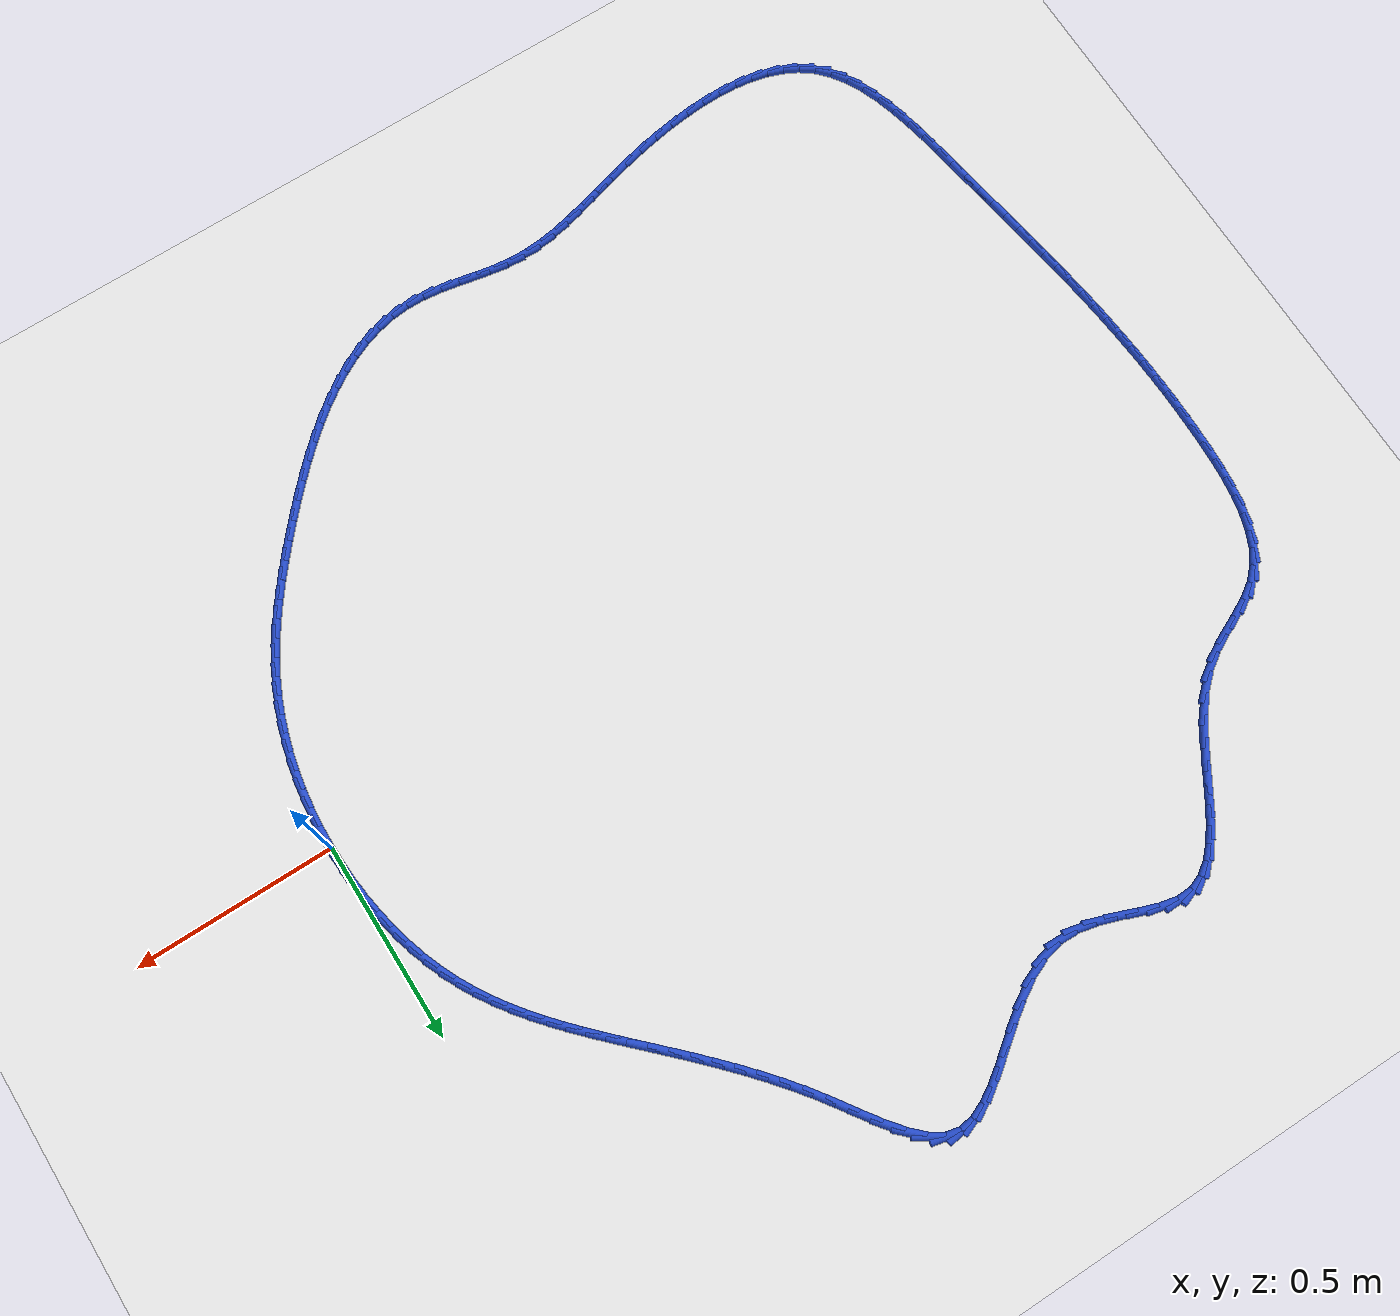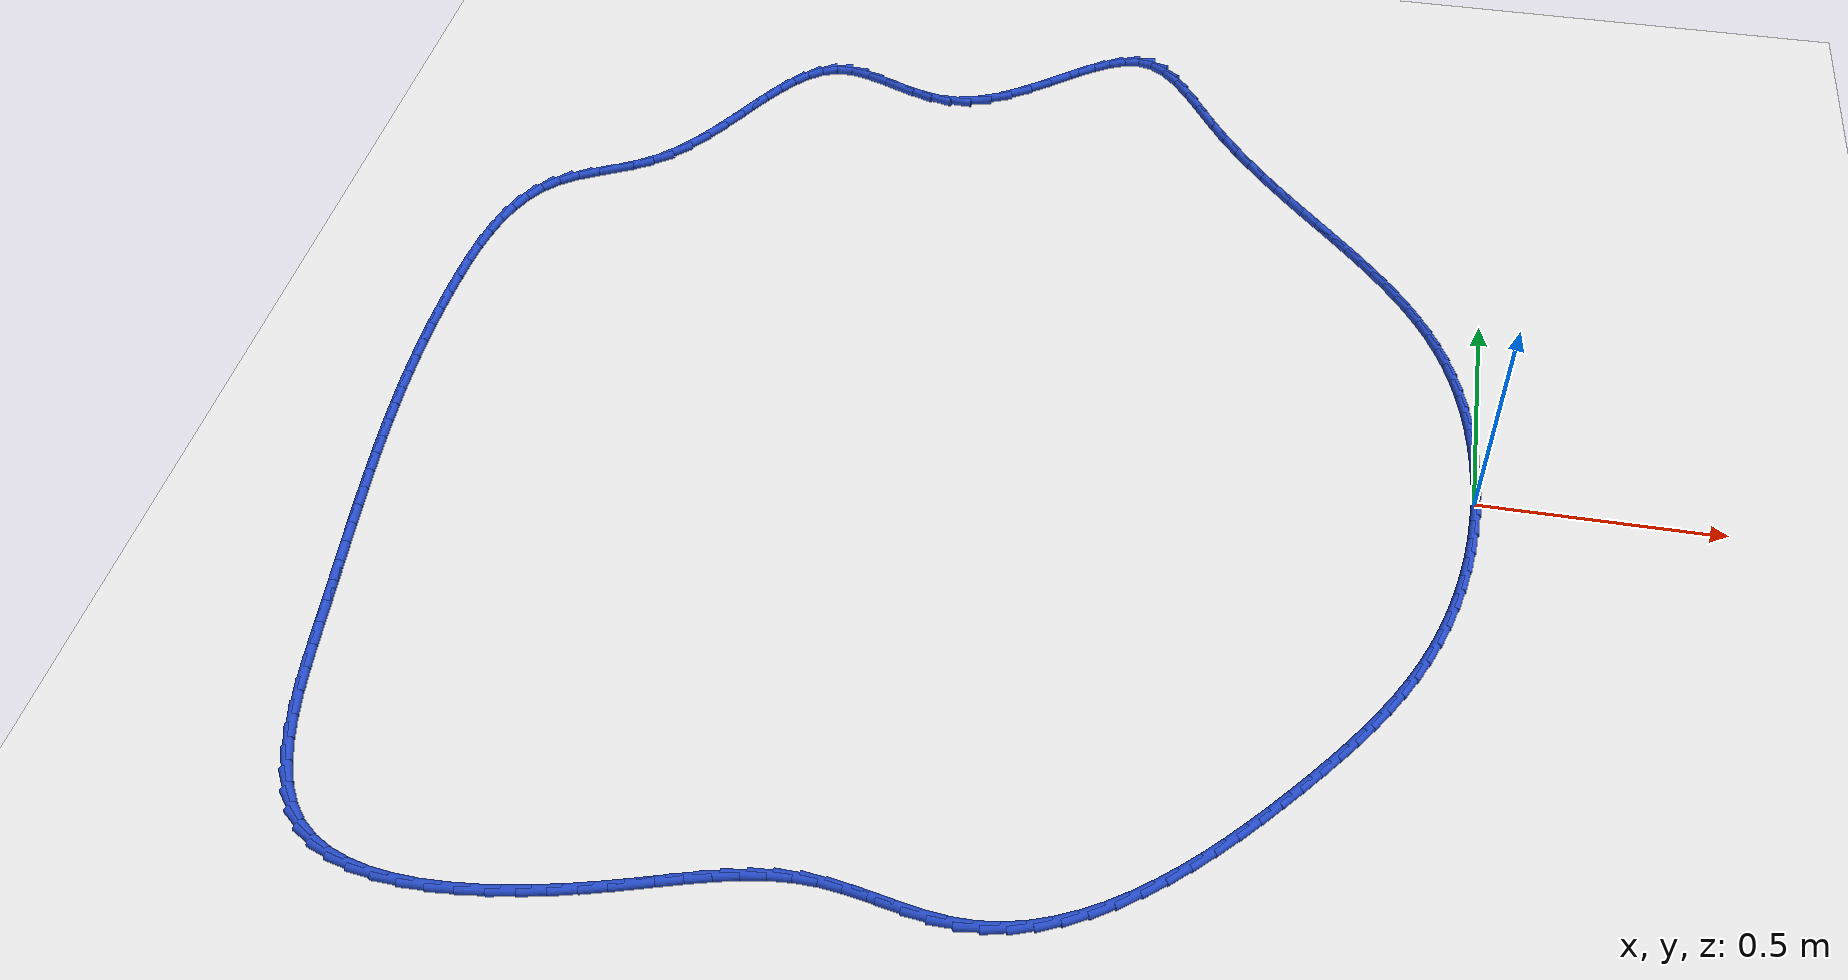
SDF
<sdf version="1.6">
 <world name="default">
  <light name="sun" type="directional">
   <pose>0 0 10 0 -0 0</pose>
   <diffuse>0.8 0.8 0.8 1</diffuse>
   <specular>0.2 0.2 0.2 1</specular>
   <attenuation>
    <range>1000</range>
    <constant>0.9</constant>
    <linear>0.01</linear>
    <quadratic>0.001</quadratic>
   </attenuation>
   <direction>-0.5 0.1 -0.9</direction>
  </light>
  <model name="ground_plane">
   <static>1</static>
   <link name="link">
    <collision name="collision">
     <geometry><plane><normal>0 0 1</normal><size>100 100</size></plane></geometry>
     <surface><friction><ode><mu>100</mu><mu2>50</mu2></ode></friction></surface>
    </collision>
    <visual name="visual">
     <cast_shadows>0</cast_shadows>
     <geometry><plane><normal>0 0 1</normal><size>100 100</size></plane></geometry>
     <material>
      <script><uri>file://media/materials/scripts/gazebo.material</uri><name>Gazebo/WhiteGlow</name></script>
     </material>
    </visual>
   </link>
  </model>
  <gravity>0 0 -9.8</gravity>
  <magnetic_field>6e-06 2.3e-05 -4.2e-05</magnetic_field>
  <atmosphere type="adiabatic"/>
  <physics name="default_physics" default="0" type="ode">
   <max_step_size>0.001</max_step_size>
   <real_time_factor>1</real_time_factor>
   <real_time_update_rate>1000</real_time_update_rate>
  </physics>
  <scene><ambient>0.4 0.4 0.4 1</ambient><background>0.7 0.7 0.7 1</background><shadows>1</shadows></scene>
  <spherical_coordinates>
   <surface_model>EARTH_WGS84</surface_model>
   <latitude_deg>0</latitude_deg>
   <longitude_deg>0</longitude_deg>
   <elevation>0</elevation>
   <heading_deg>0</heading_deg>
  </spherical_coordinates>
  <model name="line">
   <link name="link_0">
    <pose>-3.122502256758253e-17 -4.163336342344337e-17 0.01 0 1.57 -1.548435429837742</pose>
    <collision name="collision">
     <geometry><cylinder><radius>0.01</radius><length>0.08</length></cylinder></geometry>
    </collision>
    <visual name="visual">
     <material>
      <script><name>Gazebo/Blue</name><uri>file://media/materials/scripts/gazebo.material</uri></script>
     </material>
     <geometry><cylinder><radius>0.01</radius><length>0.08</length></cylinder></geometry>
    </visual>
   </link>
   <link name="link_1">
    <pose>-0.0010797746106219251 0.04828047107234886 0.01 0 1.57 -1.502948068944316</pose>
    <collision name="collision">
     <geometry><cylinder><radius>0.01</radius><length>0.08</length></cylinder></geometry>
    </collision>
    <visual name="visual">
     <material>
      <script><name>Gazebo/Blue</name><uri>file://media/materials/scripts/gazebo.material</uri></script>
     </material>
     <geometry><cylinder><radius>0.01</radius><length>0.08</length></cylinder></geometry>
    </visual>
   </link>
   <link name="link_2">
    <pose>-0.00435417076018637 0.09646697244958875 0.01 0 1.57 -1.4568380785739359</pose>
    <collision name="collision">
     <geometry><cylinder><radius>0.01</radius><length>0.08</length></cylinder></geometry>
    </collision>
    <visual name="visual">
     <material>
      <script><name>Gazebo/Blue</name><uri>file://media/materials/scripts/gazebo.material</uri></script>
     </material>
     <geometry><cylinder><radius>0.01</radius><length>0.08</length></cylinder></geometry>
    </visual>
   </link>
   <link name="link_3">
    <pose>-0.00983034954563554 0.14431302913071556 0.01 0 1.57 -1.4095907758107686</pose>
    <collision name="collision">
     <geometry><cylinder><radius>0.01</radius><length>0.08</length></cylinder></geometry>
    </collision>
    <visual name="visual">
     <material>
      <script><name>Gazebo/Blue</name><uri>file://media/materials/scripts/gazebo.material</uri></script>
     </material>
     <geometry><cylinder><radius>0.01</radius><length>0.08</length></cylinder></geometry>
    </visual>
   </link>
   <link name="link_4">
    <pose>-0.01751547206391159 0.19157216611472505 0.01 0 1.57 -1.3606741259340653</pose>
    <collision name="collision">
     <geometry><cylinder><radius>0.01</radius><length>0.08</length></cylinder></geometry>
    </collision>
    <visual name="visual">
     <material>
      <script><name>Gazebo/Blue</name><uri>file://media/materials/scripts/gazebo.material</uri></script>
     </material>
     <geometry><cylinder><radius>0.01</radius><length>0.08</length></cylinder></geometry>
    </visual>
   </link>
   <link name="link_5">
    <pose>-0.0274166994119567 0.2379979084006133 0.01 0 1.57 -1.309529851118331</pose>
    <collision name="collision">
     <geometry><cylinder><radius>0.01</radius><length>0.08</length></cylinder></geometry>
    </collision>
    <visual name="visual">
     <material>
      <script><name>Gazebo/Blue</name><uri>file://media/materials/scripts/gazebo.material</uri></script>
     </material>
     <geometry><cylinder><radius>0.01</radius><length>0.08</length></cylinder></geometry>
    </visual>
   </link>
   <link name="link_6">
    <pose>-0.039541192686713064 0.2833437809873762 0.01 0 1.57 -1.255566710921567</pose>
    <collision name="collision">
     <geometry><cylinder><radius>0.01</radius><length>0.08</length></cylinder></geometry>
    </collision>
    <visual name="visual">
     <material>
      <script><name>Gazebo/Blue</name><uri>file://media/materials/scripts/gazebo.material</uri></script>
     </material>
     <geometry><cylinder><radius>0.01</radius><length>0.08</length></cylinder></geometry>
    </visual>
   </link>
   <link name="link_7">
    <pose>-0.05389611298512284 0.3273633088740096 0.01 0 1.57 -1.1981574657107663</pose>
    <collision name="collision">
     <geometry><cylinder><radius>0.01</radius><length>0.08</length></cylinder></geometry>
    </collision>
    <visual name="visual">
     <material>
      <script><name>Gazebo/Blue</name><uri>file://media/materials/scripts/gazebo.material</uri></script>
     </material>
     <geometry><cylinder><radius>0.01</radius><length>0.08</length></cylinder></geometry>
    </visual>
   </link>
   <link name="link_8">
    <pose>-0.07048862140412818 0.36981001705950933 0.01 0 1.57 -1.1370663758819282</pose>
    <collision name="collision">
     <geometry><cylinder><radius>0.01</radius><length>0.08</length></cylinder></geometry>
    </collision>
    <visual name="visual">
     <material>
      <script><name>Gazebo/Blue</name><uri>file://media/materials/scripts/gazebo.material</uri></script>
     </material>
     <geometry><cylinder><radius>0.01</radius><length>0.08</length></cylinder></geometry>
    </visual>
   </link>
   <link name="link_9">
    <pose>-0.08931663055004367 0.4104626846287461 0.01 0 1.57 -1.076639368212078</pose>
    <collision name="collision">
     <geometry><cylinder><radius>0.01</radius><length>0.08</length></cylinder></geometry>
    </collision>
    <visual name="visual">
     <material>
      <script><name>Gazebo/Blue</name><uri>file://media/materials/scripts/gazebo.material</uri></script>
     </material>
     <geometry><cylinder><radius>0.01</radius><length>0.08</length></cylinder></geometry>
    </visual>
   </link>
   <link name="link_10">
    <pose>-0.11027853460510091 0.449371837368738 0.01 0 1.57 -1.0205103860366862</pose>
    <collision name="collision">
     <geometry><cylinder><radius>0.01</radius><length>0.08</length></cylinder></geometry>
    </collision>
    <visual name="visual">
     <material>
      <script><name>Gazebo/Blue</name><uri>file://media/materials/scripts/gazebo.material</uri></script>
     </material>
     <geometry><cylinder><radius>0.01</radius><length>0.08</length></cylinder></geometry>
    </visual>
   </link>
   <link name="link_11">
    <pose>-0.13321212555456896 0.4867534824566995 0.01 0 1.57 -0.9695946165859214</pose>
    <collision name="collision">
     <geometry><cylinder><radius>0.01</radius><length>0.08</length></cylinder></geometry>
    </collision>
    <visual name="visual">
     <material>
      <script><name>Gazebo/Blue</name><uri>file://media/materials/scripts/gazebo.material</uri></script>
     </material>
     <geometry><cylinder><radius>0.01</radius><length>0.08</length></cylinder></geometry>
    </visual>
   </link>
   <link name="link_12">
    <pose>-0.15795433555531685 0.5228259749319056 0.01 0 1.57 -0.9245294212496116</pose>
    <collision name="collision">
     <geometry><cylinder><radius>0.01</radius><length>0.08</length></cylinder></geometry>
    </collision>
    <visual name="visual">
     <material>
      <script><name>Gazebo/Blue</name><uri>file://media/materials/scripts/gazebo.material</uri></script>
     </material>
     <geometry><cylinder><radius>0.01</radius><length>0.08</length></cylinder></geometry>
    </visual>
   </link>
   <link name="link_13">
    <pose>-0.18434209676421345 0.5578076698336305 0.01 0 1.57 -0.8857226603805859</pose>
    <collision name="collision">
     <geometry><cylinder><radius>0.01</radius><length>0.08</length></cylinder></geometry>
    </collision>
    <visual name="visual">
     <material>
      <script><name>Gazebo/Blue</name><uri>file://media/materials/scripts/gazebo.material</uri></script>
     </material>
     <geometry><cylinder><radius>0.01</radius><length>0.08</length></cylinder></geometry>
    </visual>
   </link>
   <link name="link_14">
    <pose>-0.2122123413381279 0.5919169222011492 0.01 0 1.57 -0.8533835240218439</pose>
    <collision name="collision">
     <geometry><cylinder><radius>0.01</radius><length>0.08</length></cylinder></geometry>
    </collision>
    <visual name="visual">
     <material>
      <script><name>Gazebo/Blue</name><uri>file://media/materials/scripts/gazebo.material</uri></script>
     </material>
     <geometry><cylinder><radius>0.01</radius><length>0.08</length></cylinder></geometry>
    </visual>
   </link>
   <link name="link_15">
    <pose>-0.24140200143392912 0.6253720870737358 0.01 0 1.57 -0.8275637358968018</pose>
    <collision name="collision">
     <geometry><cylinder><radius>0.01</radius><length>0.08</length></cylinder></geometry>
    </collision>
    <visual name="visual">
     <material>
      <script><name>Gazebo/Blue</name><uri>file://media/materials/scripts/gazebo.material</uri></script>
     </material>
     <geometry><cylinder><radius>0.01</radius><length>0.08</length></cylinder></geometry>
    </visual>
   </link>
   <link name="link_16">
    <pose>-0.2717480092084861 0.6583915194906651 0.01 0 1.57 -0.8081995863498982</pose>
    <collision name="collision">
     <geometry><cylinder><radius>0.01</radius><length>0.08</length></cylinder></geometry>
    </collision>
    <visual name="visual">
     <material>
      <script><name>Gazebo/Blue</name><uri>file://media/materials/scripts/gazebo.material</uri></script>
     </material>
     <geometry><cylinder><radius>0.01</radius><length>0.08</length></cylinder></geometry>
    </visual>
   </link>
   <link name="link_17">
    <pose>-0.30308729681866786 0.6911935744912113 0.01 0 1.57 -0.7951486367421489</pose>
    <collision name="collision">
     <geometry><cylinder><radius>0.01</radius><length>0.08</length></cylinder></geometry>
    </collision>
    <visual name="visual">
     <material>
      <script><name>Gazebo/Blue</name><uri>file://media/materials/scripts/gazebo.material</uri></script>
     </material>
     <geometry><cylinder><radius>0.01</radius><length>0.08</length></cylinder></geometry>
    </visual>
   </link>
   <link name="link_18">
    <pose>-0.3352567964213432 0.7239966071146492 0.01 0 1.57 -0.7882181426831398</pose>
    <collision name="collision">
     <geometry><cylinder><radius>0.01</radius><length>0.08</length></cylinder></geometry>
    </collision>
    <visual name="visual">
     <material>
      <script><name>Gazebo/Blue</name><uri>file://media/materials/scripts/gazebo.material</uri></script>
     </material>
     <geometry><cylinder><radius>0.01</radius><length>0.08</length></cylinder></geometry>
    </visual>
   </link>
   <link name="link_19">
    <pose>-0.3680934401733815 0.7570189724002535 0.01 0 1.57 -0.7871845619134492</pose>
    <collision name="collision">
     <geometry><cylinder><radius>0.01</radius><length>0.08</length></cylinder></geometry>
    </collision>
    <visual name="visual">
     <material>
      <script><name>Gazebo/Blue</name><uri>file://media/materials/scripts/gazebo.material</uri></script>
     </material>
     <geometry><cylinder><radius>0.01</radius><length>0.08</length></cylinder></geometry>
    </visual>
   </link>
   <link name="link_20">
    <pose>-0.40143416023165135 0.7904790253872984 0.01 0 1.57 -0.7918048773027135</pose>
    <collision name="collision">
     <geometry><cylinder><radius>0.01</radius><length>0.08</length></cylinder></geometry>
    </collision>
    <visual name="visual">
     <material>
      <script><name>Gazebo/Blue</name><uri>file://media/materials/scripts/gazebo.material</uri></script>
     </material>
     <geometry><cylinder><radius>0.01</radius><length>0.08</length></cylinder></geometry>
    </visual>
   </link>
   <link name="link_21">
    <pose>-0.4351158887530221 0.8245951211150587 0.01 0 1.57 -0.8018211122325916</pose>
    <collision name="collision">
     <geometry><cylinder><radius>0.01</radius><length>0.08</length></cylinder></geometry>
    </collision>
    <visual name="visual">
     <material>
      <script><name>Gazebo/Blue</name><uri>file://media/materials/scripts/gazebo.material</uri></script>
     </material>
     <geometry><cylinder><radius>0.01</radius><length>0.08</length></cylinder></geometry>
    </visual>
   </link>
   <link name="link_22">
    <pose>-0.46897555789436235 0.8595856146228088 0.01 0 1.57 -0.8169596382863726</pose>
    <collision name="collision">
     <geometry><cylinder><radius>0.01</radius><length>0.08</length></cylinder></geometry>
    </collision>
    <visual name="visual">
     <material>
      <script><name>Gazebo/Blue</name><uri>file://media/materials/scripts/gazebo.material</uri></script>
     </material>
     <geometry><cylinder><radius>0.01</radius><length>0.08</length></cylinder></geometry>
    </visual>
   </link>
   <link name="link_23">
    <pose>-0.5028500998125415 0.8956688609498233 0.01 0 1.57 -0.8369269062319549</pose>
    <collision name="collision">
     <geometry><cylinder><radius>0.01</radius><length>0.08</length></cylinder></geometry>
    </collision>
    <visual name="visual">
     <material>
      <script><name>Gazebo/Blue</name><uri>file://media/materials/scripts/gazebo.material</uri></script>
     </material>
     <geometry><cylinder><radius>0.01</radius><length>0.08</length></cylinder></geometry>
    </visual>
   </link>
   <link name="link_24">
    <pose>-0.5365764466644282 0.9330632151353768 0.01 0 1.57 -0.861403209362557</pose>
    <collision name="collision">
     <geometry><cylinder><radius>0.01</radius><length>0.08</length></cylinder></geometry>
    </collision>
    <visual name="visual">
     <material>
      <script><name>Gazebo/Blue</name><uri>file://media/materials/scripts/gazebo.material</uri></script>
     </material>
     <geometry><cylinder><radius>0.01</radius><length>0.08</length></cylinder></geometry>
    </visual>
   </link>
   <link name="link_25">
    <pose>-0.5699915306068915 0.9719870322187436 0.01 0 1.57 -0.8900360650598279</pose>
    <collision name="collision">
     <geometry><cylinder><radius>0.01</radius><length>0.08</length></cylinder></geometry>
    </collision>
    <visual name="visual">
     <material>
      <script><name>Gazebo/Blue</name><uri>file://media/materials/scripts/gazebo.material</uri></script>
     </material>
     <geometry><cylinder><radius>0.01</radius><length>0.08</length></cylinder></geometry>
    </visual>
   </link>
   <link name="link_26">
    <pose>-0.6029322837968005 1.0126586672391982 0.01 0 1.57 -0.9224347609188671</pose>
    <collision name="collision">
     <geometry><cylinder><radius>0.01</radius><length>0.08</length></cylinder></geometry>
    </collision>
    <visual name="visual">
     <material>
      <script><name>Gazebo/Blue</name><uri>file://media/materials/scripts/gazebo.material</uri></script>
     </material>
     <geometry><cylinder><radius>0.01</radius><length>0.08</length></cylinder></geometry>
    </visual>
   </link>
   <link name="link_27">
    <pose>-0.6352356383910243 1.0552964752360157 0.01 0 1.57 -0.9564537085518491</pose>
    <collision name="collision">
     <geometry><cylinder><radius>0.01</radius><length>0.08</length></cylinder></geometry>
    </collision>
    <visual name="visual">
     <material>
      <script><name>Gazebo/Blue</name><uri>file://media/materials/scripts/gazebo.material</uri></script>
     </material>
     <geometry><cylinder><radius>0.01</radius><length>0.08</length></cylinder></geometry>
    </visual>
   </link>
   <link name="link_28">
    <pose>-0.6667643967040539 1.0999925992749575 0.01 0 1.57 -0.9706035646979716</pose>
    <collision name="collision">
     <geometry><cylinder><radius>0.01</radius><length>0.08</length></cylinder></geometry>
    </collision>
    <visual name="visual">
     <material>
      <script><name>Gazebo/Blue</name><uri>file://media/materials/scripts/gazebo.material</uri></script>
     </material>
     <geometry><cylinder><radius>0.01</radius><length>0.08</length></cylinder></geometry>
    </visual>
   </link>
   <link name="link_29">
    <pose>-0.6977145591325691 1.1452136187844102 0.01 0 1.57 -0.9501591068908417</pose>
    <collision name="collision">
     <geometry><cylinder><radius>0.01</radius><length>0.08</length></cylinder></geometry>
    </collision>
    <visual name="visual">
     <material>
      <script><name>Gazebo/Blue</name><uri>file://media/materials/scripts/gazebo.material</uri></script>
     </material>
     <geometry><cylinder><radius>0.01</radius><length>0.08</length></cylinder></geometry>
    </visual>
   </link>
   <link name="link_30">
    <pose>-0.728513581017587 1.1882969207954595 0.01 0 1.57 -0.8885804075570896</pose>
    <collision name="collision">
     <geometry><cylinder><radius>0.01</radius><length>0.08</length></cylinder></geometry>
    </collision>
    <visual name="visual">
     <material>
      <script><name>Gazebo/Blue</name><uri>file://media/materials/scripts/gazebo.material</uri></script>
     </material>
     <geometry><cylinder><radius>0.01</radius><length>0.08</length></cylinder></geometry>
    </visual>
   </link>
   <link name="link_31">
    <pose>-0.7595935886170481 1.2265571044748194 0.01 0 1.57 -0.7687483526286377</pose>
    <collision name="collision">
     <geometry><cylinder><radius>0.01</radius><length>0.08</length></cylinder></geometry>
    </collision>
    <visual name="visual">
     <material>
      <script><name>Gazebo/Blue</name><uri>file://media/materials/scripts/gazebo.material</uri></script>
     </material>
     <geometry><cylinder><radius>0.01</radius><length>0.08</length></cylinder></geometry>
    </visual>
   </link>
   <link name="link_32">
    <pose>-0.7913867081888931 1.2573087689892033 0.01 0 1.57 -0.5579718634683034</pose>
    <collision name="collision">
     <geometry><cylinder><radius>0.01</radius><length>0.08</length></cylinder></geometry>
    </collision>
    <visual name="visual">
     <material>
      <script><name>Gazebo/Blue</name><uri>file://media/materials/scripts/gazebo.material</uri></script>
     </material>
     <geometry><cylinder><radius>0.01</radius><length>0.08</length></cylinder></geometry>
    </visual>
   </link>
   <link name="link_33">
    <pose>-0.8243250659910629 1.277866513505326 0.01 0 1.57 -0.22212326100522212</pose>
    <collision name="collision">
     <geometry><cylinder><radius>0.01</radius><length>0.08</length></cylinder></geometry>
    </collision>
    <visual name="visual">
     <material>
      <script><name>Gazebo/Blue</name><uri>file://media/materials/scripts/gazebo.material</uri></script>
     </material>
     <geometry><cylinder><radius>0.01</radius><length>0.08</length></cylinder></geometry>
    </visual>
   </link>
   <link name="link_34">
    <pose>-0.8588290491676992 1.2856592353440464 0.01 0 1.57 0.13807156750440358</pose>
    <collision name="collision">
     <geometry><cylinder><radius>0.01</radius><length>0.08</length></cylinder></geometry>
    </collision>
    <visual name="visual">
     <material>
      <script><name>Gazebo/Blue</name><uri>file://media/materials/scripts/gazebo.material</uri></script>
     </material>
     <geometry><cylinder><radius>0.01</radius><length>0.08</length></cylinder></geometry>
    </visual>
   </link>
   <link name="link_35">
    <pose>-0.8950613847110209 1.280624545879579 0.01 0 1.57 0.3880358079131005</pose>
    <collision name="collision">
     <geometry><cylinder><radius>0.01</radius><length>0.08</length></cylinder></geometry>
    </collision>
    <visual name="visual">
     <material>
      <script><name>Gazebo/Blue</name><uri>file://media/materials/scripts/gazebo.material</uri></script>
     </material>
     <geometry><cylinder><radius>0.01</radius><length>0.08</length></cylinder></geometry>
    </visual>
   </link>
   <link name="link_36">
    <pose>-0.9329338138076455 1.2651437856115377 0.01 0 1.57 0.5366027221303381</pose>
    <collision name="collision">
     <geometry><cylinder><radius>0.01</radius><length>0.08</length></cylinder></geometry>
    </collision>
    <visual name="visual">
     <material>
      <script><name>Gazebo/Blue</name><uri>file://media/materials/scripts/gazebo.material</uri></script>
     </material>
     <geometry><cylinder><radius>0.01</radius><length>0.08</length></cylinder></geometry>
    </visual>
   </link>
   <link name="link_37">
    <pose>-0.9723476736878953 1.2416995934016188 0.01 0 1.57 0.6160503631779193</pose>
    <collision name="collision">
     <geometry><cylinder><radius>0.01</radius><length>0.08</length></cylinder></geometry>
    </collision>
    <visual name="visual">
     <material>
      <script><name>Gazebo/Blue</name><uri>file://media/materials/scripts/gazebo.material</uri></script>
     </material>
     <geometry><cylinder><radius>0.01</radius><length>0.08</length></cylinder></geometry>
    </visual>
   </link>
   <link name="link_38">
    <pose>-1.013204301582094 1.2127746081115207 0.01 0 1.57 0.647622296973</pose>
    <collision name="collision">
     <geometry><cylinder><radius>0.01</radius><length>0.08</length></cylinder></geometry>
    </collision>
    <visual name="visual">
     <material>
      <script><name>Gazebo/Blue</name><uri>file://media/materials/scripts/gazebo.material</uri></script>
     </material>
     <geometry><cylinder><radius>0.01</radius><length>0.08</length></cylinder></geometry>
    </visual>
   </link>
   <link name="link_39">
    <pose>-1.0554050347205641 1.1808514686029408 0.01 0 1.57 0.6413472724299429</pose>
    <collision name="collision">
     <geometry><cylinder><radius>0.01</radius><length>0.08</length></cylinder></geometry>
    </collision>
    <visual name="visual">
     <material>
      <script><name>Gazebo/Blue</name><uri>file://media/materials/scripts/gazebo.material</uri></script>
     </material>
     <geometry><cylinder><radius>0.01</radius><length>0.08</length></cylinder></geometry>
    </visual>
   </link>
   <link name="link_40">
    <pose>-1.098851210333628 1.148412813737576 0.01 0 1.57 0.5994475709941217</pose>
    <collision name="collision">
     <geometry><cylinder><radius>0.01</radius><length>0.08</length></cylinder></geometry>
    </collision>
    <visual name="visual">
     <material>
      <script><name>Gazebo/Blue</name><uri>file://media/materials/scripts/gazebo.material</uri></script>
     </material>
     <geometry><cylinder><radius>0.01</radius><length>0.08</length></cylinder></geometry>
    </visual>
   </link>
   <link name="link_41">
    <pose>-1.1434441656516106 1.117941282377124 0.01 0 1.57 0.5181736623008475</pose>
    <collision name="collision">
     <geometry><cylinder><radius>0.01</radius><length>0.08</length></cylinder></geometry>
    </collision>
    <visual name="visual">
     <material>
      <script><name>Gazebo/Blue</name><uri>file://media/materials/scripts/gazebo.material</uri></script>
     </material>
     <geometry><cylinder><radius>0.01</radius><length>0.08</length></cylinder></geometry>
    </visual>
   </link>
   <link name="link_42">
    <pose>-1.1890852379048331 1.0919195133832826 0.01 0 1.57 0.3888629655359301</pose>
    <collision name="collision">
     <geometry><cylinder><radius>0.01</radius><length>0.08</length></cylinder></geometry>
    </collision>
    <visual name="visual">
     <material>
      <script><name>Gazebo/Blue</name><uri>file://media/materials/scripts/gazebo.material</uri></script>
     </material>
     <geometry><cylinder><radius>0.01</radius><length>0.08</length></cylinder></geometry>
    </visual>
   </link>
   <link name="link_43">
    <pose>-1.2356757643236196 1.0728301456177496 0.01 0 1.57 0.20116383879066754</pose>
    <collision name="collision">
     <geometry><cylinder><radius>0.01</radius><length>0.08</length></cylinder></geometry>
    </collision>
    <visual name="visual">
     <material>
      <script><name>Gazebo/Blue</name><uri>file://media/materials/scripts/gazebo.material</uri></script>
     </material>
     <geometry><cylinder><radius>0.01</radius><length>0.08</length></cylinder></geometry>
    </visual>
   </link>
   <link name="link_44">
    <pose>-1.283117082138293 1.0631558179422218 0.01 0 1.57 -0.03508029669718921</pose>
    <collision name="collision">
     <geometry><cylinder><radius>0.01</radius><length>0.08</length></cylinder></geometry>
    </collision>
    <visual name="visual">
     <material>
      <script><name>Gazebo/Blue</name><uri>file://media/materials/scripts/gazebo.material</uri></script>
     </material>
     <geometry><cylinder><radius>0.01</radius><length>0.08</length></cylinder></geometry>
    </visual>
   </link>
   <link name="link_45">
    <pose>-1.3312590786945586 1.0648453465818528 0.01 0 1.57 -0.22355577004431154</pose>
    <collision name="collision">
     <geometry><cylinder><radius>0.01</radius><length>0.08</length></cylinder></geometry>
    </collision>
    <visual name="visual">
     <material>
      <script><name>Gazebo/Blue</name><uri>file://media/materials/scripts/gazebo.material</uri></script>
     </material>
     <geometry><cylinder><radius>0.01</radius><length>0.08</length></cylinder></geometry>
    </visual>
   </link>
   <link name="link_46">
    <pose>-1.3795642185034473 1.0758278093191909 0.01 0 1.57 -0.33030439406185547</pose>
    <collision name="collision">
     <geometry><cylinder><radius>0.01</radius><length>0.08</length></cylinder></geometry>
    </collision>
    <visual name="visual">
     <material>
      <script><name>Gazebo/Blue</name><uri>file://media/materials/scripts/gazebo.material</uri></script>
     </material>
     <geometry><cylinder><radius>0.01</radius><length>0.08</length></cylinder></geometry>
    </visual>
   </link>
   <link name="link_47">
    <pose>-1.4273184737146294 1.092201072489549 0.01 0 1.57 -0.3666578080271962</pose>
    <collision name="collision">
     <geometry><cylinder><radius>0.01</radius><length>0.08</length></cylinder></geometry>
    </collision>
    <visual name="visual">
     <material>
      <script><name>Gazebo/Blue</name><uri>file://media/materials/scripts/gazebo.material</uri></script>
     </material>
     <geometry><cylinder><radius>0.01</radius><length>0.08</length></cylinder></geometry>
    </visual>
   </link>
   <link name="link_48">
    <pose>-1.473806921072066 1.1100537120704284 0.01 0 1.57 -0.3335266691055806</pose>
    <collision name="collision">
     <geometry><cylinder><radius>0.01</radius><length>0.08</length></cylinder></geometry>
    </collision>
    <visual name="visual">
     <material>
      <script><name>Gazebo/Blue</name><uri>file://media/materials/scripts/gazebo.material</uri></script>
     </material>
     <geometry><cylinder><radius>0.01</radius><length>0.08</length></cylinder></geometry>
    </visual>
   </link>
   <link name="link_49">
    <pose>-1.5183146373197172 1.125474304039331 0.01 0 1.57 -0.2137761515112165</pose>
    <collision name="collision">
     <geometry><cylinder><radius>0.01</radius><length>0.08</length></cylinder></geometry>
    </collision>
    <visual name="visual">
     <material>
      <script><name>Gazebo/Blue</name><uri>file://media/materials/scripts/gazebo.material</uri></script>
     </material>
     <geometry><cylinder><radius>0.01</radius><length>0.08</length></cylinder></geometry>
    </visual>
   </link>
   <link name="link_50">
    <pose>-1.5601266992015428 1.1345514243737571 0.01 0 1.57 0.0283785797063838</pose>
    <collision name="collision">
     <geometry><cylinder><radius>0.01</radius><length>0.08</length></cylinder></geometry>
    </collision>
    <visual name="visual">
     <material>
      <script><name>Gazebo/Blue</name><uri>file://media/materials/scripts/gazebo.material</uri></script>
     </material>
     <geometry><cylinder><radius>0.01</radius><length>0.08</length></cylinder></geometry>
    </visual>
   </link>
   <link name="link_51">
    <pose>-1.5985497778082318 1.1334607391670468 0.01 0 1.57 0.34462796720672234</pose>
    <collision name="collision">
     <geometry><cylinder><radius>0.01</radius><length>0.08</length></cylinder></geometry>
    </collision>
    <visual name="visual">
     <material>
      <script><name>Gazebo/Blue</name><uri>file://media/materials/scripts/gazebo.material</uri></script>
     </material>
     <geometry><cylinder><radius>0.01</radius><length>0.08</length></cylinder></geometry>
    </visual>
   </link>
   <link name="link_52">
    <pose>-1.6335180821489232 1.1209087782937548 0.01 0 1.57 0.6093030647202164</pose>
    <collision name="collision">
     <geometry><cylinder><radius>0.01</radius><length>0.08</length></cylinder></geometry>
    </collision>
    <visual name="visual">
     <material>
      <script><name>Gazebo/Blue</name><uri>file://media/materials/scripts/gazebo.material</uri></script>
     </material>
     <geometry><cylinder><radius>0.01</radius><length>0.08</length></cylinder></geometry>
    </visual>
   </link>
   <link name="link_53">
    <pose>-1.6656760254222533 1.0984663289228764 0.01 0 1.57 0.7949274883063177</pose>
    <collision name="collision">
     <geometry><cylinder><radius>0.01</radius><length>0.08</length></cylinder></geometry>
    </collision>
    <visual name="visual">
     <material>
      <script><name>Gazebo/Blue</name><uri>file://media/materials/scripts/gazebo.material</uri></script>
     </material>
     <geometry><cylinder><radius>0.01</radius><length>0.08</length></cylinder></geometry>
    </visual>
   </link>
   <link name="link_54">
    <pose>-1.6957062278364077 1.0678582672972519 0.01 0 1.57 0.9136438831790281</pose>
    <collision name="collision">
     <geometry><cylinder><radius>0.01</radius><length>0.08</length></cylinder></geometry>
    </collision>
    <visual name="visual">
     <material>
      <script><name>Gazebo/Blue</name><uri>file://media/materials/scripts/gazebo.material</uri></script>
     </material>
     <geometry><cylinder><radius>0.01</radius><length>0.08</length></cylinder></geometry>
    </visual>
   </link>
   <link name="link_55">
    <pose>-1.724291309599572 1.0308094696597208 0.01 0 1.57 0.9831340081159935</pose>
    <collision name="collision">
     <geometry><cylinder><radius>0.01</radius><length>0.08</length></cylinder></geometry>
    </collision>
    <visual name="visual">
     <material>
      <script><name>Gazebo/Blue</name><uri>file://media/materials/scripts/gazebo.material</uri></script>
     </material>
     <geometry><cylinder><radius>0.01</radius><length>0.08</length></cylinder></geometry>
    </visual>
   </link>
   <link name="link_56">
    <pose>-1.7521138909199319 0.9890448122531216 0.01 0 1.57 1.0158941542658542</pose>
    <collision name="collision">
     <geometry><cylinder><radius>0.01</radius><length>0.08</length></cylinder></geometry>
    </collision>
    <visual name="visual">
     <material>
      <script><name>Gazebo/Blue</name><uri>file://media/materials/scripts/gazebo.material</uri></script>
     </material>
     <geometry><cylinder><radius>0.01</radius><length>0.08</length></cylinder></geometry>
    </visual>
   </link>
   <link name="link_57">
    <pose>-1.7798565920056721 0.9442891713202944 0.01 0 1.57 1.018757428790506</pose>
    <collision name="collision">
     <geometry><cylinder><radius>0.01</radius><length>0.08</length></cylinder></geometry>
    </collision>
    <visual name="visual">
     <material>
      <script><name>Gazebo/Blue</name><uri>file://media/materials/scripts/gazebo.material</uri></script>
     </material>
     <geometry><cylinder><radius>0.01</radius><length>0.08</length></cylinder></geometry>
    </visual>
   </link>
   <link name="link_58">
    <pose>-1.8082020330649786 0.898267423104078 0.01 0 1.57 0.9941917937083741</pose>
    <collision name="collision">
     <geometry><cylinder><radius>0.01</radius><length>0.08</length></cylinder></geometry>
    </collision>
    <visual name="visual">
     <material>
      <script><name>Gazebo/Blue</name><uri>file://media/materials/scripts/gazebo.material</uri></script>
     </material>
     <geometry><cylinder><radius>0.01</radius><length>0.08</length></cylinder></geometry>
    </visual>
   </link>
   <link name="link_59">
    <pose>-1.8378328343060366 0.8527044438473126 0.01 0 1.57 0.9412439397898769</pose>
    <collision name="collision">
     <geometry><cylinder><radius>0.01</radius><length>0.08</length></cylinder></geometry>
    </collision>
    <visual name="visual">
     <material>
      <script><name>Gazebo/Blue</name><uri>file://media/materials/scripts/gazebo.material</uri></script>
     </material>
     <geometry><cylinder><radius>0.01</radius><length>0.08</length></cylinder></geometry>
    </visual>
   </link>
   <link name="link_60">
    <pose>-1.8694316159370319 0.8093251097928374 0.01 0 1.57 0.8561077616490715</pose>
    <collision name="collision">
     <geometry><cylinder><radius>0.01</radius><length>0.08</length></cylinder></geometry>
    </collision>
    <visual name="visual">
     <material>
      <script><name>Gazebo/Blue</name><uri>file://media/materials/scripts/gazebo.material</uri></script>
     </material>
     <geometry><cylinder><radius>0.01</radius><length>0.08</length></cylinder></geometry>
    </visual>
   </link>
   <link name="link_61">
    <pose>-1.9036809981661496 0.7698542971834913 0.01 0 1.57 0.7330072373649285</pose>
    <collision name="collision">
     <geometry><cylinder><radius>0.01</radius><length>0.08</length></cylinder></geometry>
    </collision>
    <visual name="visual">
     <material>
      <script><name>Gazebo/Blue</name><uri>file://media/materials/scripts/gazebo.material</uri></script>
     </material>
     <geometry><cylinder><radius>0.01</radius><length>0.08</length></cylinder></geometry>
    </visual>
   </link>
   <link name="link_62">
    <pose>-1.9412636012015758 0.7360168822621146 0.01 0 1.57 0.5811434411380837</pose>
    <collision name="collision">
     <geometry><cylinder><radius>0.01</radius><length>0.08</length></cylinder></geometry>
    </collision>
    <visual name="visual">
     <material>
      <script><name>Gazebo/Blue</name><uri>file://media/materials/scripts/gazebo.material</uri></script>
     </material>
     <geometry><cylinder><radius>0.01</radius><length>0.08</length></cylinder></geometry>
    </visual>
   </link>
   <link name="link_63">
    <pose>-1.9824907852861735 0.7089387056081264 0.01 0 1.57 0.47345387876281536</pose>
    <collision name="collision">
     <geometry><cylinder><radius>0.01</radius><length>0.08</length></cylinder></geometry>
    </collision>
    <visual name="visual">
     <material>
      <script><name>Gazebo/Blue</name><uri>file://media/materials/scripts/gazebo.material</uri></script>
     </material>
     <geometry><cylinder><radius>0.01</radius><length>0.08</length></cylinder></geometry>
    </visual>
   </link>
   <link name="link_64">
    <pose>-2.025813441250407 0.6867437017705974 0.01 0 1.57 0.43521179561273854</pose>
    <collision name="collision">
     <geometry><cylinder><radius>0.01</radius><length>0.08</length></cylinder></geometry>
    </collision>
    <visual name="visual">
     <material>
      <script><name>Gazebo/Blue</name><uri>file://media/materials/scripts/gazebo.material</uri></script>
     </material>
     <geometry><cylinder><radius>0.01</radius><length>0.08</length></cylinder></geometry>
    </visual>
   </link>
   <link name="link_65">
    <pose>-2.0691009011688686 0.666617448169676 0.01 0 1.57 0.4696901879516021</pose>
    <collision name="collision">
     <geometry><cylinder><radius>0.01</radius><length>0.08</length></cylinder></geometry>
    </collision>
    <visual name="visual">
     <material>
      <script><name>Gazebo/Blue</name><uri>file://media/materials/scripts/gazebo.material</uri></script>
     </material>
     <geometry><cylinder><radius>0.01</radius><length>0.08</length></cylinder></geometry>
    </visual>
   </link>
   <link name="link_66">
    <pose>-2.110222300188062 0.6457452044779565 0.01 0 1.57 0.5858058856590932</pose>
    <collision name="collision">
     <geometry><cylinder><radius>0.01</radius><length>0.08</length></cylinder></geometry>
    </collision>
    <visual name="visual">
     <material>
      <script><name>Gazebo/Blue</name><uri>file://media/materials/scripts/gazebo.material</uri></script>
     </material>
     <geometry><cylinder><radius>0.01</radius><length>0.08</length></cylinder></geometry>
    </visual>
   </link>
   <link name="link_67">
    <pose>-2.1470467734544916 0.6213122303680326 0.01 0 1.57 0.7815354891608881</pose>
    <collision name="collision">
     <geometry><cylinder><radius>0.01</radius><length>0.08</length></cylinder></geometry>
    </collision>
    <visual name="visual">
     <material>
      <script><name>Gazebo/Blue</name><uri>file://media/materials/scripts/gazebo.material</uri></script>
     </material>
     <geometry><cylinder><radius>0.01</radius><length>0.08</length></cylinder></geometry>
    </visual>
   </link>
   <link name="link_68">
    <pose>-2.177720723925913 0.5908743362183856 0.01 0 1.57 0.9788627321762867</pose>
    <collision name="collision">
     <geometry><cylinder><radius>0.01</radius><length>0.08</length></cylinder></geometry>
    </collision>
    <visual name="visual">
     <material>
      <script><name>Gazebo/Blue</name><uri>file://media/materials/scripts/gazebo.material</uri></script>
     </material>
     <geometry><cylinder><radius>0.01</radius><length>0.08</length></cylinder></geometry>
    </visual>
   </link>
   <link name="link_69">
    <pose>-2.2022215283176996 0.55443431179284 0.01 0 1.57 1.1400210119796954</pose>
    <collision name="collision">
     <geometry><cylinder><radius>0.01</radius><length>0.08</length></cylinder></geometry>
    </collision>
    <visual name="visual">
     <material>
      <script><name>Gazebo/Blue</name><uri>file://media/materials/scripts/gazebo.material</uri></script>
     </material>
     <geometry><cylinder><radius>0.01</radius><length>0.08</length></cylinder></geometry>
    </visual>
   </link>
   <link name="link_70">
    <pose>-2.221268980267725 0.5129871396144724 0.01 0 1.57 1.2656913137448729</pose>
    <collision name="collision">
     <geometry><cylinder><radius>0.01</radius><length>0.08</length></cylinder></geometry>
    </collision>
    <visual name="visual">
     <material>
      <script><name>Gazebo/Blue</name><uri>file://media/materials/scripts/gazebo.material</uri></script>
     </material>
     <geometry><cylinder><radius>0.01</radius><length>0.08</length></cylinder></geometry>
    </visual>
   </link>
   <link name="link_71">
    <pose>-2.2355849912898944 0.46753063261228855 0.01 0 1.57 1.3612722500029204</pose>
    <collision name="collision">
     <geometry><cylinder><radius>0.01</radius><length>0.08</length></cylinder></geometry>
    </collision>
    <visual name="visual">
     <material>
      <script><name>Gazebo/Blue</name><uri>file://media/materials/scripts/gazebo.material</uri></script>
     </material>
     <geometry><cylinder><radius>0.01</radius><length>0.08</length></cylinder></geometry>
    </visual>
   </link>
   <link name="link_72">
    <pose>-2.245891472898108 0.4190626037152952 0.01 0 1.57 1.4326443309962547</pose>
    <collision name="collision">
     <geometry><cylinder><radius>0.01</radius><length>0.08</length></cylinder></geometry>
    </collision>
    <visual name="visual">
     <material>
      <script><name>Gazebo/Blue</name><uri>file://media/materials/scripts/gazebo.material</uri></script>
     </material>
     <geometry><cylinder><radius>0.01</radius><length>0.08</length></cylinder></geometry>
    </visual>
   </link>
   <link name="link_73">
    <pose>-2.2529103366062695 0.36858086585249755 0.01 0 1.57 1.484537854411256</pose>
    <collision name="collision">
     <geometry><cylinder><radius>0.01</radius><length>0.08</length></cylinder></geometry>
    </collision>
    <visual name="visual">
     <material>
      <script><name>Gazebo/Blue</name><uri>file://media/materials/scripts/gazebo.material</uri></script>
     </material>
     <geometry><cylinder><radius>0.01</radius><length>0.08</length></cylinder></geometry>
    </visual>
   </link>
   <link name="link_74">
    <pose>-2.25736349392828 0.3170832319529028 0.01 0 1.57 1.5201878037773906</pose>
    <collision name="collision">
     <geometry><cylinder><radius>0.01</radius><length>0.08</length></cylinder></geometry>
    </collision>
    <visual name="visual">
     <material>
      <script><name>Gazebo/Blue</name><uri>file://media/materials/scripts/gazebo.material</uri></script>
     </material>
     <geometry><cylinder><radius>0.01</radius><length>0.08</length></cylinder></geometry>
    </visual>
   </link>
   <link name="link_75">
    <pose>-2.2599728563780443 0.2655675149455166 0.01 0 1.57 1.5424325096397702</pose>
    <collision name="collision">
     <geometry><cylinder><radius>0.01</radius><length>0.08</length></cylinder></geometry>
    </collision>
    <visual name="visual">
     <material>
      <script><name>Gazebo/Blue</name><uri>file://media/materials/scripts/gazebo.material</uri></script>
     </material>
     <geometry><cylinder><radius>0.01</radius><length>0.08</length></cylinder></geometry>
    </visual>
   </link>
   <link name="link_76">
    <pose>-2.2614090478918443 0.21494645982918356 0.01 0 1.57 1.560375229400733</pose>
    <collision name="collision">
     <geometry><cylinder><radius>0.01</radius><length>0.08</length></cylinder></geometry>
    </collision>
    <visual name="visual">
     <material>
      <script><name>Gazebo/Blue</name><uri>file://media/materials/scripts/gazebo.material</uri></script>
     </material>
     <geometry><cylinder><radius>0.01</radius><length>0.08</length></cylinder></geometry>
    </visual>
   </link>
   <link name="link_77">
    <pose>-2.2619249784983526 0.16543997214397216 0.01 0 1.57 -1.5634799647741016</pose>
    <collision name="collision">
     <geometry><cylinder><radius>0.01</radius><length>0.08</length></cylinder></geometry>
    </collision>
    <visual name="visual">
     <material>
      <script><name>Gazebo/Blue</name><uri>file://media/materials/scripts/gazebo.material</uri></script>
     </material>
     <geometry><cylinder><radius>0.01</radius><length>0.08</length></cylinder></geometry>
    </visual>
   </link>
   <link name="link_78">
    <pose>-2.2615700587487435 0.11693042385665033 0.01 0 1.57 -1.546076128135567</pose>
    <collision name="collision">
     <geometry><cylinder><radius>0.01</radius><length>0.08</length></cylinder></geometry>
    </collision>
    <visual name="visual">
     <material>
      <script><name>Gazebo/Blue</name><uri>file://media/materials/scripts/gazebo.material</uri></script>
     </material>
     <geometry><cylinder><radius>0.01</radius><length>0.08</length></cylinder></geometry>
    </visual>
   </link>
   <link name="link_79">
    <pose>-2.2603923339440697 0.06929792246747794 0.01 0 1.57 -1.5291676945719606</pose>
    <collision name="collision">
     <geometry><cylinder><radius>0.01</radius><length>0.08</length></cylinder></geometry>
    </collision>
    <visual name="visual">
     <material>
      <script><name>Gazebo/Blue</name><uri>file://media/materials/scripts/gazebo.material</uri></script>
     </material>
     <geometry><cylinder><radius>0.01</radius><length>0.08</length></cylinder></geometry>
    </visual>
   </link>
   <link name="link_80">
    <pose>-2.2584398493853843 0.022422575476713672 0.01 0 1.57 -1.5129174894336377</pose>
    <collision name="collision">
     <geometry><cylinder><radius>0.01</radius><length>0.08</length></cylinder></geometry>
    </collision>
    <visual name="visual">
     <material>
      <script><name>Gazebo/Blue</name><uri>file://media/materials/scripts/gazebo.material</uri></script>
     </material>
     <geometry><cylinder><radius>0.01</radius><length>0.08</length></cylinder></geometry>
    </visual>
   </link>
   <link name="link_81">
    <pose>-2.255760650373742 -0.023815509615383437 0.01 0 1.57 -1.497484912824635</pose>
    <collision name="collision">
     <geometry><cylinder><radius>0.01</radius><length>0.08</length></cylinder></geometry>
    </collision>
    <visual name="visual">
     <material>
      <script><name>Gazebo/Blue</name><uri>file://media/materials/scripts/gazebo.material</uri></script>
     </material>
     <geometry><cylinder><radius>0.01</radius><length>0.08</length></cylinder></geometry>
    </visual>
   </link>
   <link name="link_82">
    <pose>-2.252402782210193 -0.06953622530855506 0.01 0 1.57 -1.4830214054293869</pose>
    <collision name="collision">
     <geometry><cylinder><radius>0.01</radius><length>0.08</length></cylinder></geometry>
    </collision>
    <visual name="visual">
     <material>
      <script><name>Gazebo/Blue</name><uri>file://media/materials/scripts/gazebo.material</uri></script>
     </material>
     <geometry><cylinder><radius>0.01</radius><length>0.08</length></cylinder></geometry>
    </visual>
   </link>
   <link name="link_83">
    <pose>-2.248414290195795 -0.11485946410254058 0.01 0 1.57 -1.469666112955214</pose>
    <collision name="collision">
     <geometry><cylinder><radius>0.01</radius><length>0.08</length></cylinder></geometry>
    </collision>
    <visual name="visual">
     <material>
      <script><name>Gazebo/Blue</name><uri>file://media/materials/scripts/gazebo.material</uri></script>
     </material>
     <geometry><cylinder><radius>0.01</radius><length>0.08</length></cylinder></geometry>
    </visual>
   </link>
   <link name="link_84">
    <pose>-2.243843219631598 -0.15990511849708175 0.01 0 1.57 -1.4575419984768954</pose>
    <collision name="collision">
     <geometry><cylinder><radius>0.01</radius><length>0.08</length></cylinder></geometry>
    </collision>
    <visual name="visual">
     <material>
      <script><name>Gazebo/Blue</name><uri>file://media/materials/scripts/gazebo.material</uri></script>
     </material>
     <geometry><cylinder><radius>0.01</radius><length>0.08</length></cylinder></geometry>
    </visual>
   </link>
   <link name="link_85">
    <pose>-2.2387376158186565 -0.20479308099191934 0.01 0 1.57 -1.4467526139761469</pose>
    <collision name="collision">
     <geometry><cylinder><radius>0.01</radius><length>0.08</length></cylinder></geometry>
    </collision>
    <visual name="visual">
     <material>
      <script><name>Gazebo/Blue</name><uri>file://media/materials/scripts/gazebo.material</uri></script>
     </material>
     <geometry><cylinder><radius>0.01</radius><length>0.08</length></cylinder></geometry>
    </visual>
   </link>
   <link name="link_86">
    <pose>-2.233145524058023 -0.2496432440867945 0.01 0 1.57 -1.4373796855796264</pose>
    <collision name="collision">
     <geometry><cylinder><radius>0.01</radius><length>0.08</length></cylinder></geometry>
    </collision>
    <visual name="visual">
     <material>
      <script><name>Gazebo/Blue</name><uri>file://media/materials/scripts/gazebo.material</uri></script>
     </material>
     <geometry><cylinder><radius>0.01</radius><length>0.08</length></cylinder></geometry>
    </visual>
   </link>
   <link name="link_87">
    <pose>-2.227114989650752 -0.29457550028144874 0.01 0 1.57 -1.4294815998349941</pose>
    <collision name="collision">
     <geometry><cylinder><radius>0.01</radius><length>0.08</length></cylinder></geometry>
    </collision>
    <visual name="visual">
     <material>
      <script><name>Gazebo/Blue</name><uri>file://media/materials/scripts/gazebo.material</uri></script>
     </material>
     <geometry><cylinder><radius>0.01</radius><length>0.08</length></cylinder></geometry>
    </visual>
   </link>
   <link name="link_88">
    <pose>-2.2206940578978953 -0.33970974207562155 0.01 0 1.57 -1.423092809874306</pose>
    <collision name="collision">
     <geometry><cylinder><radius>0.01</radius><length>0.08</length></cylinder></geometry>
    </collision>
    <visual name="visual">
     <material>
      <script><name>Gazebo/Blue</name><uri>file://media/materials/scripts/gazebo.material</uri></script>
     </material>
     <geometry><cylinder><radius>0.01</radius><length>0.08</length></cylinder></geometry>
    </visual>
   </link>
   <link name="link_89">
    <pose>-2.213930774100508 -0.38516586196905456 0.01 0 1.57 -1.4182241184023472</pose>
    <collision name="collision">
     <geometry><cylinder><radius>0.01</radius><length>0.08</length></cylinder></geometry>
    </collision>
    <visual name="visual">
     <material>
      <script><name>Gazebo/Blue</name><uri>file://media/materials/scripts/gazebo.material</uri></script>
     </material>
     <geometry><cylinder><radius>0.01</radius><length>0.08</length></cylinder></geometry>
    </visual>
   </link>
   <link name="link_90">
    <pose>-2.206873183559642 -0.43106375246148865 0.01 0 1.57 -1.4148637447181027</pose>
    <collision name="collision">
     <geometry><cylinder><radius>0.01</radius><length>0.08</length></cylinder></geometry>
    </collision>
    <visual name="visual">
     <material>
      <script><name>Gazebo/Blue</name><uri>file://media/materials/scripts/gazebo.material</uri></script>
     </material>
     <geometry><cylinder><radius>0.01</radius><length>0.08</length></cylinder></geometry>
    </visual>
   </link>
   <link name="link_91">
    <pose>-2.199569331576351 -0.4775233060526649 0.01 0 1.57 -1.41297904825412</pose>
    <collision name="collision">
     <geometry><cylinder><radius>0.01</radius><length>0.08</length></cylinder></geometry>
    </collision>
    <visual name="visual">
     <material>
      <script><name>Gazebo/Blue</name><uri>file://media/materials/scripts/gazebo.material</uri></script>
     </material>
     <geometry><cylinder><radius>0.01</radius><length>0.08</length></cylinder></geometry>
    </visual>
   </link>
   <link name="link_92">
    <pose>-2.1920672634516887 -0.5246644152423251 0.01 0 1.57 -1.4125187616838484</pose>
    <collision name="collision">
     <geometry><cylinder><radius>0.01</radius><length>0.08</length></cylinder></geometry>
    </collision>
    <visual name="visual">
     <material>
      <script><name>Gazebo/Blue</name><uri>file://media/materials/scripts/gazebo.material</uri></script>
     </material>
     <geometry><cylinder><radius>0.01</radius><length>0.08</length></cylinder></geometry>
    </visual>
   </link>
   <link name="link_93">
    <pose>-2.1844150244867073 -0.5726069725302082 0.01 0 1.57 -1.4134155808753943</pose>
    <collision name="collision">
     <geometry><cylinder><radius>0.01</radius><length>0.08</length></cylinder></geometry>
    </collision>
    <visual name="visual">
     <material>
      <script><name>Gazebo/Blue</name><uri>file://media/materials/scripts/gazebo.material</uri></script>
     </material>
     <geometry><cylinder><radius>0.01</radius><length>0.08</length></cylinder></geometry>
    </visual>
   </link>
   <link name="link_94">
    <pose>-2.1766606599824607 -0.6214708704160561 0.01 0 1.57 -1.4154036676558068</pose>
    <collision name="collision">
     <geometry><cylinder><radius>0.01</radius><length>0.08</length></cylinder></geometry>
    </collision>
    <visual name="visual">
     <material>
      <script><name>Gazebo/Blue</name><uri>file://media/materials/scripts/gazebo.material</uri></script>
     </material>
     <geometry><cylinder><radius>0.01</radius><length>0.08</length></cylinder></geometry>
    </visual>
   </link>
   <link name="link_95">
    <pose>-2.1688445721902183 -0.6713643142465805 0.01 0 1.57 -1.4125819866820302</pose>
    <collision name="collision">
     <geometry><cylinder><radius>0.01</radius><length>0.08</length></cylinder></geometry>
    </collision>
    <visual name="visual">
     <material>
      <script><name>Gazebo/Blue</name><uri>file://media/materials/scripts/gazebo.material</uri></script>
     </material>
     <geometry><cylinder><radius>0.01</radius><length>0.08</length></cylinder></geometry>
    </visual>
   </link>
   <link name="link_96">
    <pose>-2.160762376350012 -0.7220212002457802 0.01 0 1.57 -1.3981416262491067</pose>
    <collision name="collision">
     <geometry><cylinder><radius>0.01</radius><length>0.08</length></cylinder></geometry>
    </collision>
    <visual name="visual">
     <material>
      <script><name>Gazebo/Blue</name><uri>file://media/materials/scripts/gazebo.material</uri></script>
     </material>
     <geometry><cylinder><radius>0.01</radius><length>0.08</length></cylinder></geometry>
    </visual>
   </link>
   <link name="link_97">
    <pose>-2.1519190444662315 -0.772730995768619 0.01 0 1.57 -1.371265715701458</pose>
    <collision name="collision">
     <geometry><cylinder><radius>0.01</radius><length>0.08</length></cylinder></geometry>
    </collision>
    <visual name="visual">
     <material>
      <script><name>Gazebo/Blue</name><uri>file://media/materials/scripts/gazebo.material</uri></script>
     </material>
     <geometry><cylinder><radius>0.01</radius><length>0.08</length></cylinder></geometry>
    </visual>
   </link>
   <link name="link_98">
    <pose>-2.1418026494004114 -0.8227573273245674 0.01 0 1.57 -1.3306689092431807</pose>
    <collision name="collision">
     <geometry><cylinder><radius>0.01</radius><length>0.08</length></cylinder></geometry>
    </collision>
    <visual name="visual">
     <material>
      <script><name>Gazebo/Blue</name><uri>file://media/materials/scripts/gazebo.material</uri></script>
     </material>
     <geometry><cylinder><radius>0.01</radius><length>0.08</length></cylinder></geometry>
    </visual>
   </link>
   <link name="link_99">
    <pose>-2.1299012640140838 -0.8713638214230937 0.01 0 1.57 -1.2741489050392283</pose>
    <collision name="collision">
     <geometry><cylinder><radius>0.01</radius><length>0.08</length></cylinder></geometry>
    </collision>
    <visual name="visual">
     <material>
      <script><name>Gazebo/Blue</name><uri>file://media/materials/scripts/gazebo.material</uri></script>
     </material>
     <geometry><cylinder><radius>0.01</radius><length>0.08</length></cylinder></geometry>
    </visual>
   </link>
   <link name="link_100">
    <pose>-2.1157029611687843 -0.9178141045736675 0.01 0 1.57 -1.1985488452214001</pose>
    <collision name="collision">
     <geometry><cylinder><radius>0.01</radius><length>0.08</length></cylinder></geometry>
    </collision>
    <visual name="visual">
     <material>
      <script><name>Gazebo/Blue</name><uri>file://media/materials/scripts/gazebo.material</uri></script>
     </material>
     <geometry><cylinder><radius>0.01</radius><length>0.08</length></cylinder></geometry>
    </visual>
   </link>
   <link name="link_101">
    <pose>-2.098695813726044 -0.9613718032857581 0.01 0 1.57 -1.0998913249662168</pose>
    <collision name="collision">
     <geometry><cylinder><radius>0.01</radius><length>0.08</length></cylinder></geometry>
    </collision>
    <visual name="visual">
     <material>
      <script><name>Gazebo/Blue</name><uri>file://media/materials/scripts/gazebo.material</uri></script>
     </material>
     <geometry><cylinder><radius>0.01</radius><length>0.08</length></cylinder></geometry>
    </visual>
   </link>
   <link name="link_102">
    <pose>-2.078367894547398 -1.0013005440688332 0.01 0 1.57 -0.9740524283631989</pose>
    <collision name="collision">
     <geometry><cylinder><radius>0.01</radius><length>0.08</length></cylinder></geometry>
    </collision>
    <visual name="visual">
     <material>
      <script><name>Gazebo/Blue</name><uri>file://media/materials/scripts/gazebo.material</uri></script>
     </material>
     <geometry><cylinder><radius>0.01</radius><length>0.08</length></cylinder></geometry>
    </visual>
   </link>
   <link name="link_103">
    <pose>-2.0542072764943793 -1.036863953432362 0.01 0 1.57 -0.8185649495480781</pose>
    <collision name="collision">
     <geometry><cylinder><radius>0.01</radius><length>0.08</length></cylinder></geometry>
    </collision>
    <visual name="visual">
     <material>
      <script><name>Gazebo/Blue</name><uri>file://media/materials/scripts/gazebo.material</uri></script>
     </material>
     <geometry><cylinder><radius>0.01</radius><length>0.08</length></cylinder></geometry>
    </visual>
   </link>
   <link name="link_104">
    <pose>-2.0257020330193067 -1.0673256585257191 0.01 0 1.57 -0.6423265684801623</pose>
    <collision name="collision">
     <geometry><cylinder><radius>0.01</radius><length>0.08</length></cylinder></geometry>
    </collision>
    <visual name="visual">
     <material>
      <script><name>Gazebo/Blue</name><uri>file://media/materials/scripts/gazebo.material</uri></script>
     </material>
     <geometry><cylinder><radius>0.01</radius><length>0.08</length></cylinder></geometry>
    </visual>
   </link>
   <link name="link_105">
    <pose>-1.9925240112538956 -1.0921483394681444 0.01 0 1.57 -0.4778368472108875</pose>
    <collision name="collision">
     <geometry><cylinder><radius>0.01</radius><length>0.08</length></cylinder></geometry>
    </collision>
    <visual name="visual">
     <material>
      <script><name>Gazebo/Blue</name><uri>file://media/materials/scripts/gazebo.material</uri></script>
     </material>
     <geometry><cylinder><radius>0.01</radius><length>0.08</length></cylinder></geometry>
    </visual>
   </link>
   <link name="link_106">
    <pose>-1.955047858163429 -1.111555908316743 0.01 0 1.57 -0.33596664318415437</pose>
    <collision name="collision">
     <geometry><cylinder><radius>0.01</radius><length>0.08</length></cylinder></geometry>
    </collision>
    <visual name="visual">
     <material>
      <script><name>Gazebo/Blue</name><uri>file://media/materials/scripts/gazebo.material</uri></script>
     </material>
     <geometry><cylinder><radius>0.01</radius><length>0.08</length></cylinder></geometry>
    </visual>
   </link>
   <link name="link_107">
    <pose>-1.9138161986520914 -1.1259542210703175 0.01 0 1.57 -0.21691755482066813</pose>
    <collision name="collision">
     <geometry><cylinder><radius>0.01</radius><length>0.08</length></cylinder></geometry>
    </collision>
    <visual name="visual">
     <material>
      <script><name>Gazebo/Blue</name><uri>file://media/materials/scripts/gazebo.material</uri></script>
     </material>
     <geometry><cylinder><radius>0.01</radius><length>0.08</length></cylinder></geometry>
    </visual>
   </link>
   <link name="link_108">
    <pose>-1.869371657624063 -1.1357491337276713 0.01 0 1.57 -0.11824852669775256</pose>
    <collision name="collision">
     <geometry><cylinder><radius>0.01</radius><length>0.08</length></cylinder></geometry>
    </collision>
    <visual name="visual">
     <material>
      <script><name>Gazebo/Blue</name><uri>file://media/materials/scripts/gazebo.material</uri></script>
     </material>
     <geometry><cylinder><radius>0.01</radius><length>0.08</length></cylinder></geometry>
    </visual>
   </link>
   <link name="link_109">
    <pose>-1.822256859983526 -1.1413465022876077 0.01 0 1.57 -0.03665277715489067</pose>
    <collision name="collision">
     <geometry><cylinder><radius>0.01</radius><length>0.08</length></cylinder></geometry>
    </collision>
    <visual name="visual">
     <material>
      <script><name>Gazebo/Blue</name><uri>file://media/materials/scripts/gazebo.material</uri></script>
     </material>
     <geometry><cylinder><radius>0.01</radius><length>0.08</length></cylinder></geometry>
    </visual>
   </link>
   <link name="link_110">
    <pose>-1.773014430634663 -1.1431521827489297 0.01 0 1.57 0.031078546976350766</pose>
    <collision name="collision">
     <geometry><cylinder><radius>0.01</radius><length>0.08</length></cylinder></geometry>
    </collision>
    <visual name="visual">
     <material>
      <script><name>Gazebo/Blue</name><uri>file://media/materials/scripts/gazebo.material</uri></script>
     </material>
     <geometry><cylinder><radius>0.01</radius><length>0.08</length></cylinder></geometry>
    </visual>
   </link>
   <link name="link_111">
    <pose>-1.7221869944816546 -1.1415720311104411 0.01 0 1.57 0.08768940494568092</pose>
    <collision name="collision">
     <geometry><cylinder><radius>0.01</radius><length>0.08</length></cylinder></geometry>
    </collision>
    <visual name="visual">
     <material>
      <script><name>Gazebo/Blue</name><uri>file://media/materials/scripts/gazebo.material</uri></script>
     </material>
     <geometry><cylinder><radius>0.01</radius><length>0.08</length></cylinder></geometry>
    </visual>
   </link>
   <link name="link_112">
    <pose>-1.6703171764286846 -1.1370119033709447 0.01 0 1.57 0.13539540191953736</pose>
    <collision name="collision">
     <geometry><cylinder><radius>0.01</radius><length>0.08</length></cylinder></geometry>
    </collision>
    <visual name="visual">
     <material>
      <script><name>Gazebo/Blue</name><uri>file://media/materials/scripts/gazebo.material</uri></script>
     </material>
     <geometry><cylinder><radius>0.01</radius><length>0.08</length></cylinder></geometry>
    </visual>
   </link>
   <link name="link_113">
    <pose>-1.6179476013799339 -1.1298776555292434 0.01 0 1.57 0.1759393703837438</pose>
    <collision name="collision">
     <geometry><cylinder><radius>0.01</radius><length>0.08</length></cylinder></geometry>
    </collision>
    <visual name="visual">
     <material>
      <script><name>Gazebo/Blue</name><uri>file://media/materials/scripts/gazebo.material</uri></script>
     </material>
     <geometry><cylinder><radius>0.01</radius><length>0.08</length></cylinder></geometry>
    </visual>
   </link>
   <link name="link_114">
    <pose>-1.5656208942395846 -1.1205751435841407 0.01 0 1.57 0.21067784483512947</pose>
    <collision name="collision">
     <geometry><cylinder><radius>0.01</radius><length>0.08</length></cylinder></geometry>
    </collision>
    <visual name="visual">
     <material>
      <script><name>Gazebo/Blue</name><uri>file://media/materials/scripts/gazebo.material</uri></script>
     </material>
     <geometry><cylinder><radius>0.01</radius><length>0.08</length></cylinder></geometry>
    </visual>
   </link>
   <link name="link_115">
    <pose>-1.5138796799118188 -1.1095102235344398 0.01 0 1.57 0.2406635629087464</pose>
    <collision name="collision">
     <geometry><cylinder><radius>0.01</radius><length>0.08</length></cylinder></geometry>
    </collision>
    <visual name="visual">
     <material>
      <script><name>Gazebo/Blue</name><uri>file://media/materials/scripts/gazebo.material</uri></script>
     </material>
     <geometry><cylinder><radius>0.01</radius><length>0.08</length></cylinder></geometry>
    </visual>
   </link>
   <link name="link_116">
    <pose>-1.4632665833008174 -1.0970887513789436 0.01 0 1.57 0.26554833582462595</pose>
    <collision name="collision">
     <geometry><cylinder><radius>0.01</radius><length>0.08</length></cylinder></geometry>
    </collision>
    <visual name="visual">
     <material>
      <script><name>Gazebo/Blue</name><uri>file://media/materials/scripts/gazebo.material</uri></script>
     </material>
     <geometry><cylinder><radius>0.01</radius><length>0.08</length></cylinder></geometry>
    </visual>
   </link>
   <link name="link_117">
    <pose>-1.414236177151545 -1.083753885037229 0.01 0 1.57 0.27792191367625496</pose>
    <collision name="collision">
     <geometry><cylinder><radius>0.01</radius><length>0.08</length></cylinder></geometry>
    </collision>
    <visual name="visual">
     <material>
      <script><name>Gazebo/Blue</name><uri>file://media/materials/scripts/gazebo.material</uri></script>
     </material>
     <geometry><cylinder><radius>0.01</radius><length>0.08</length></cylinder></geometry>
    </visual>
   </link>
   <link name="link_118">
    <pose>-1.3666820717290697 -1.0701864254142077 0.01 0 1.57 0.27366366633313216</pose>
    <collision name="collision">
     <geometry><cylinder><radius>0.01</radius><length>0.08</length></cylinder></geometry>
    </collision>
    <visual name="visual">
     <material>
      <script><name>Gazebo/Blue</name><uri>file://media/materials/scripts/gazebo.material</uri></script>
     </material>
     <geometry><cylinder><radius>0.01</radius><length>0.08</length></cylinder></geometry>
    </visual>
   </link>
   <link name="link_119">
    <pose>-1.3202777408231217 -1.0571604307912732 0.01 0 1.57 0.2514691078736101</pose>
    <collision name="collision">
     <geometry><cylinder><radius>0.01</radius><length>0.08</length></cylinder></geometry>
    </collision>
    <visual name="visual">
     <material>
      <script><name>Gazebo/Blue</name><uri>file://media/materials/scripts/gazebo.material</uri></script>
     </material>
     <geometry><cylinder><radius>0.01</radius><length>0.08</length></cylinder></geometry>
    </visual>
   </link>
   <link name="link_120">
    <pose>-1.2746961383367117 -1.045450179691702 0.01 0 1.57 0.2102228812965906</pose>
    <collision name="collision">
     <geometry><cylinder><radius>0.01</radius><length>0.08</length></cylinder></geometry>
    </collision>
    <visual name="visual">
     <material>
      <script><name>Gazebo/Blue</name><uri>file://media/materials/scripts/gazebo.material</uri></script>
     </material>
     <geometry><cylinder><radius>0.01</radius><length>0.08</length></cylinder></geometry>
    </visual>
   </link>
   <link name="link_121">
    <pose>-1.2296102181728499 -1.0358299506387691 0.01 0 1.57 0.14928915559007194</pose>
    <collision name="collision">
     <geometry><cylinder><radius>0.01</radius><length>0.08</length></cylinder></geometry>
    </collision>
    <visual name="visual">
     <material>
      <script><name>Gazebo/Blue</name><uri>file://media/materials/scripts/gazebo.material</uri></script>
     </material>
     <geometry><cylinder><radius>0.01</radius><length>0.08</length></cylinder></geometry>
    </visual>
   </link>
   <link name="link_122">
    <pose>-1.184692934234549 -1.029074022155751 0.01 0 1.57 0.06904815898811317</pose>
    <collision name="collision">
     <geometry><cylinder><radius>0.01</radius><length>0.08</length></cylinder></geometry>
    </collision>
    <visual name="visual">
     <material>
      <script><name>Gazebo/Blue</name><uri>file://media/materials/scripts/gazebo.material</uri></script>
     </material>
     <geometry><cylinder><radius>0.01</radius><length>0.08</length></cylinder></geometry>
    </visual>
   </link>
   <link name="link_123">
    <pose>-1.1396172404248195 -1.025956672765924 0.01 0 1.57 -0.028369986479351624</pose>
    <collision name="collision">
     <geometry><cylinder><radius>0.01</radius><length>0.08</length></cylinder></geometry>
    </collision>
    <visual name="visual">
     <material>
      <script><name>Gazebo/Blue</name><uri>file://media/materials/scripts/gazebo.material</uri></script>
     </material>
     <geometry><cylinder><radius>0.01</radius><length>0.08</length></cylinder></geometry>
    </visual>
   </link>
   <link name="link_124">
    <pose>-1.0940566698154017 -1.0272495724227906 0.01 0 1.57 -0.12361960008797047</pose>
    <collision name="collision">
     <geometry><cylinder><radius>0.01</radius><length>0.08</length></cylinder></geometry>
    </collision>
    <visual name="visual">
     <material>
      <script><name>Gazebo/Blue</name><uri>file://media/materials/scripts/gazebo.material</uri></script>
     </material>
     <geometry><cylinder><radius>0.01</radius><length>0.08</length></cylinder></geometry>
    </visual>
   </link>
   <link name="link_125">
    <pose>-1.047847541694813 -1.0329912036993996 0.01 0 1.57 -0.18016193118482465</pose>
    <collision name="collision">
     <geometry><cylinder><radius>0.01</radius><length>0.08</length></cylinder></geometry>
    </collision>
    <visual name="visual">
     <material>
      <script><name>Gazebo/Blue</name><uri>file://media/materials/scripts/gazebo.material</uri></script>
     </material>
     <geometry><cylinder><radius>0.01</radius><length>0.08</length></cylinder></geometry>
    </visual>
   </link>
   <link name="link_126">
    <pose>-1.0012113164456802 -1.0414853777974085 0.01 0 1.57 -0.19621269740891664</pose>
    <collision name="collision">
     <geometry><cylinder><radius>0.01</radius><length>0.08</length></cylinder></geometry>
    </collision>
    <visual name="visual">
     <material>
      <script><name>Gazebo/Blue</name><uri>file://media/materials/scripts/gazebo.material</uri></script>
     </material>
     <geometry><cylinder><radius>0.01</radius><length>0.08</length></cylinder></geometry>
    </visual>
   </link>
   <link name="link_127">
    <pose>-0.9544251463648621 -1.0507850701320351 0.01 0 1.57 -0.17309734104516106</pose>
    <collision name="collision">
     <geometry><cylinder><radius>0.01</radius><length>0.08</length></cylinder></geometry>
    </collision>
    <visual name="visual">
     <material>
      <script><name>Gazebo/Blue</name><uri>file://media/materials/scripts/gazebo.material</uri></script>
     </material>
     <geometry><cylinder><radius>0.01</radius><length>0.08</length></cylinder></geometry>
    </visual>
   </link>
   <link name="link_128">
    <pose>-0.9077661837492138 -1.0589432561184964 0.01 0 1.57 -0.10916750858214504</pose>
    <collision name="collision">
     <geometry><cylinder><radius>0.01</radius><length>0.08</length></cylinder></geometry>
    </collision>
    <visual name="visual">
     <material>
      <script><name>Gazebo/Blue</name><uri>file://media/materials/scripts/gazebo.material</uri></script>
     </material>
     <geometry><cylinder><radius>0.01</radius><length>0.08</length></cylinder></geometry>
    </visual>
   </link>
   <link name="link_129">
    <pose>-0.8615115808955935 -1.0640129111720107 0.01 0 1.57 -0.0028360003192431224</pose>
    <collision name="collision">
     <geometry><cylinder><radius>0.01</radius><length>0.08</length></cylinder></geometry>
    </collision>
    <visual name="visual">
     <material>
      <script><name>Gazebo/Blue</name><uri>file://media/materials/scripts/gazebo.material</uri></script>
     </material>
     <geometry><cylinder><radius>0.01</radius><length>0.08</length></cylinder></geometry>
    </visual>
   </link>
   <link name="link_130">
    <pose>-0.8159283660335959 -1.0641421855304918 0.01 0 1.57 0.11899752996683975</pose>
    <collision name="collision">
     <geometry><cylinder><radius>0.01</radius><length>0.08</length></cylinder></geometry>
    </collision>
    <visual name="visual">
     <material>
      <script><name>Gazebo/Blue</name><uri>file://media/materials/scripts/gazebo.material</uri></script>
     </material>
     <geometry><cylinder><radius>0.01</radius><length>0.08</length></cylinder></geometry>
    </visual>
   </link>
   <link name="link_131">
    <pose>-0.7711443805248095 -1.05878770409343 0.01 0 1.57 0.23297175436412454</pose>
    <collision name="collision">
     <geometry><cylinder><radius>0.01</radius><length>0.08</length></cylinder></geometry>
    </collision>
    <visual name="visual">
     <material>
      <script><name>Gazebo/Blue</name><uri>file://media/materials/scripts/gazebo.material</uri></script>
     </material>
     <geometry><cylinder><radius>0.01</radius><length>0.08</length></cylinder></geometry>
    </visual>
   </link>
   <link name="link_132">
    <pose>-0.7271862807858008 -1.0483573161006188 0.01 0 1.57 0.3364528969940407</pose>
    <collision name="collision">
     <geometry><cylinder><radius>0.01</radius><length>0.08</length></cylinder></geometry>
    </collision>
    <visual name="visual">
     <material>
      <script><name>Gazebo/Blue</name><uri>file://media/materials/scripts/gazebo.material</uri></script>
     </material>
     <geometry><cylinder><radius>0.01</radius><length>0.08</length></cylinder></geometry>
    </visual>
   </link>
   <link name="link_133">
    <pose>-0.6840784426281308 -1.0332803104140098 0.01 0 1.57 0.4285376609108989</pose>
    <collision name="collision">
     <geometry><cylinder><radius>0.01</radius><length>0.08</length></cylinder></geometry>
    </collision>
    <visual name="visual">
     <material>
      <script><name>Gazebo/Blue</name><uri>file://media/materials/scripts/gazebo.material</uri></script>
     </material>
     <geometry><cylinder><radius>0.01</radius><length>0.08</length></cylinder></geometry>
    </visual>
   </link>
   <link name="link_134">
    <pose>-0.641845241863361 -1.0139859758955538 0.01 0 1.57 0.509294622397305</pose>
    <collision name="collision">
     <geometry><cylinder><radius>0.01</radius><length>0.08</length></cylinder></geometry>
    </collision>
    <visual name="visual">
     <material>
      <script><name>Gazebo/Blue</name><uri>file://media/materials/scripts/gazebo.material</uri></script>
     </material>
     <geometry><cylinder><radius>0.01</radius><length>0.08</length></cylinder></geometry>
    </visual>
   </link>
   <link name="link_135">
    <pose>-0.6005110543030538 -0.9909036014072021 0.01 0 1.57 0.5793980240286287</pose>
    <collision name="collision">
     <geometry><cylinder><radius>0.01</radius><length>0.08</length></cylinder></geometry>
    </collision>
    <visual name="visual">
     <material>
      <script><name>Gazebo/Blue</name><uri>file://media/materials/scripts/gazebo.material</uri></script>
     </material>
     <geometry><cylinder><radius>0.01</radius><length>0.08</length></cylinder></geometry>
    </visual>
   </link>
   <link name="link_136">
    <pose>-0.5601002557587702 -0.964462475810905 0.01 0 1.57 0.6398146097615687</pose>
    <collision name="collision">
     <geometry><cylinder><radius>0.01</radius><length>0.08</length></cylinder></geometry>
    </collision>
    <visual name="visual">
     <material>
      <script><name>Gazebo/Blue</name><uri>file://media/materials/scripts/gazebo.material</uri></script>
     </material>
     <geometry><cylinder><radius>0.01</radius><length>0.08</length></cylinder></geometry>
    </visual>
   </link>
   <link name="link_137">
    <pose>-0.5206372220420733 -0.9350918879686145 0.01 0 1.57 0.6915871191601909</pose>
    <collision name="collision">
     <geometry><cylinder><radius>0.01</radius><length>0.08</length></cylinder></geometry>
    </collision>
    <visual name="visual">
     <material>
      <script><name>Gazebo/Blue</name><uri>file://media/materials/scripts/gazebo.material</uri></script>
     </material>
     <geometry><cylinder><radius>0.01</radius><length>0.08</length></cylinder></geometry>
    </visual>
   </link>
   <link name="link_138">
    <pose>-0.4821463289645245 -0.9032211267422812 0.01 0 1.57 0.7357060610081774</pose>
    <collision name="collision">
     <geometry><cylinder><radius>0.01</radius><length>0.08</length></cylinder></geometry>
    </collision>
    <visual name="visual">
     <material>
      <script><name>Gazebo/Blue</name><uri>file://media/materials/scripts/gazebo.material</uri></script>
     </material>
     <geometry><cylinder><radius>0.01</radius><length>0.08</length></cylinder></geometry>
    </visual>
   </link>
   <link name="link_139">
    <pose>-0.4446519523376855 -0.8692794809938562 0.01 0 1.57 0.7730440402386611</pose>
    <collision name="collision">
     <geometry><cylinder><radius>0.01</radius><length>0.08</length></cylinder></geometry>
    </collision>
    <visual name="visual">
     <material>
      <script><name>Gazebo/Blue</name><uri>file://media/materials/scripts/gazebo.material</uri></script>
     </material>
     <geometry><cylinder><radius>0.01</radius><length>0.08</length></cylinder></geometry>
    </visual>
   </link>
   <link name="link_140">
    <pose>-0.4081784679731183 -0.8336962395852903 0.01 0 1.57 0.804327785837854</pose>
    <collision name="collision">
     <geometry><cylinder><radius>0.01</radius><length>0.08</length></cylinder></geometry>
    </collision>
    <visual name="visual">
     <material>
      <script><name>Gazebo/Blue</name><uri>file://media/materials/scripts/gazebo.material</uri></script>
     </material>
     <geometry><cylinder><radius>0.01</radius><length>0.08</length></cylinder></geometry>
    </visual>
   </link>
   <link name="link_141">
    <pose>-0.37275025168238407 -0.7969006913785343 0.01 0 1.57 0.830129520436167</pose>
    <collision name="collision">
     <geometry><cylinder><radius>0.01</radius><length>0.08</length></cylinder></geometry>
    </collision>
    <visual name="visual">
     <material>
      <script><name>Gazebo/Blue</name><uri>file://media/materials/scripts/gazebo.material</uri></script>
     </material>
     <geometry><cylinder><radius>0.01</radius><length>0.08</length></cylinder></geometry>
    </visual>
   </link>
   <link name="link_142">
    <pose>-0.33839167927704594 -0.75932212523554 0.01 0 1.57 0.8508655558774111</pose>
    <collision name="collision">
     <geometry><cylinder><radius>0.01</radius><length>0.08</length></cylinder></geometry>
    </collision>
    <visual name="visual">
     <material>
      <script><name>Gazebo/Blue</name><uri>file://media/materials/scripts/gazebo.material</uri></script>
     </material>
     <geometry><cylinder><radius>0.01</radius><length>0.08</length></cylinder></geometry>
    </visual>
   </link>
   <link name="link_143">
    <pose>-0.3051271265686652 -0.721389830018258 0.01 0 1.57 0.8671834940476374</pose>
    <collision name="collision">
     <geometry><cylinder><radius>0.01</radius><length>0.08</length></cylinder></geometry>
    </collision>
    <visual name="visual">
     <material>
      <script><name>Gazebo/Blue</name><uri>file://media/materials/scripts/gazebo.material</uri></script>
     </material>
     <geometry><cylinder><radius>0.01</radius><length>0.08</length></cylinder></geometry>
    </visual>
   </link>
   <link name="link_144">
    <pose>-0.27298532012583465 -0.6835083423311396 0.01 0 1.57 0.8845422815577062</pose>
    <collision name="collision">
     <geometry><cylinder><radius>0.01</radius><length>0.08</length></cylinder></geometry>
    </collision>
    <visual name="visual">
     <material>
      <script><name>Gazebo/Blue</name><uri>file://media/materials/scripts/gazebo.material</uri></script>
     </material>
     <geometry><cylinder><radius>0.01</radius><length>0.08</length></cylinder></geometry>
    </visual>
   </link>
   <link name="link_145">
    <pose>-0.24205438051916836 -0.6457442953697617 0.01 0 1.57 0.9069591196855974</pose>
    <collision name="collision">
     <geometry><cylinder><radius>0.01</radius><length>0.08</length></cylinder></geometry>
    </collision>
    <visual name="visual">
     <material>
      <script><name>Gazebo/Blue</name><uri>file://media/materials/scripts/gazebo.material</uri></script>
     </material>
     <geometry><cylinder><radius>0.01</radius><length>0.08</length></cylinder></geometry>
    </visual>
   </link>
   <link name="link_146">
    <pose>-0.2124653966707006 -0.6079198674702065 0.01 0 1.57 0.934666919012305</pose>
    <collision name="collision">
     <geometry><cylinder><radius>0.01</radius><length>0.08</length></cylinder></geometry>
    </collision>
    <visual name="visual">
     <material>
      <script><name>Gazebo/Blue</name><uri>file://media/materials/scripts/gazebo.material</uri></script>
     </material>
     <geometry><cylinder><radius>0.01</radius><length>0.08</length></cylinder></geometry>
    </visual>
   </link>
   <link name="link_147">
    <pose>-0.18435041482336056 -0.5698517905938039 0.01 0 1.57 0.9677398448724861</pose>
    <collision name="collision">
     <geometry><cylinder><radius>0.01</radius><length>0.08</length></cylinder></geometry>
    </collision>
    <visual name="visual">
     <material>
      <script><name>Gazebo/Blue</name><uri>file://media/materials/scripts/gazebo.material</uri></script>
     </material>
     <geometry><cylinder><radius>0.01</radius><length>0.08</length></cylinder></geometry>
    </visual>
   </link>
   <link name="link_148">
    <pose>-0.15784148122007569 -0.5313567967018814 0.01 0 1.57 1.0061498109638294</pose>
    <collision name="collision">
     <geometry><cylinder><radius>0.01</radius><length>0.08</length></cylinder></geometry>
    </collision>
    <visual name="visual">
     <material>
      <script><name>Gazebo/Blue</name><uri>file://media/materials/scripts/gazebo.material</uri></script>
     </material>
     <geometry><cylinder><radius>0.01</radius><length>0.08</length></cylinder></geometry>
    </visual>
   </link>
   <link name="link_149">
    <pose>-0.13307064210377398 -0.49225161775576765 0.01 0 1.57 1.0497349451719278</pose>
    <collision name="collision">
     <geometry><cylinder><radius>0.01</radius><length>0.08</length></cylinder></geometry>
    </collision>
    <visual name="visual">
     <material>
      <script><name>Gazebo/Blue</name><uri>file://media/materials/scripts/gazebo.material</uri></script>
     </material>
     <geometry><cylinder><radius>0.01</radius><length>0.08</length></cylinder></geometry>
    </visual>
   </link>
   <link name="link_150">
    <pose>-0.11016994371738355 -0.4523529857167909 0.01 0 1.57 1.0981701312075238</pose>
    <collision name="collision">
     <geometry><cylinder><radius>0.01</radius><length>0.08</length></cylinder></geometry>
    </collision>
    <visual name="visual">
     <material>
      <script><name>Gazebo/Blue</name><uri>file://media/materials/scripts/gazebo.material</uri></script>
     </material>
     <geometry><cylinder><radius>0.01</radius><length>0.08</length></cylinder></geometry>
    </visual>
   </link>
   <link name="link_151">
    <pose>-0.08927143230383205 -0.41147763254627884 0.01 0 1.57 1.1509181349223787</pose>
    <collision name="collision">
     <geometry><cylinder><radius>0.01</radius><length>0.08</length></cylinder></geometry>
    </collision>
    <visual name="visual">
     <material>
      <script><name>Gazebo/Blue</name><uri>file://media/materials/scripts/gazebo.material</uri></script>
     </material>
     <geometry><cylinder><radius>0.01</radius><length>0.08</length></cylinder></geometry>
    </visual>
   </link>
   <link name="link_152">
    <pose>-0.07050646425917687 -0.3694439047839302 0.01 0 1.57 1.2054311683432268</pose>
    <collision name="collision">
     <geometry><cylinder><radius>0.01</radius><length>0.08</length></cylinder></geometry>
    </collision>
    <visual name="visual">
     <material>
      <script><name>Gazebo/Blue</name><uri>file://media/materials/scripts/gazebo.material</uri></script>
     </material>
     <geometry><cylinder><radius>0.01</radius><length>0.08</length></cylinder></geometry>
    </visual>
   </link>
   <link name="link_153">
    <pose>-0.05395777437547643 -0.326183947253286 0.01 0 1.57 1.2583963382223153</pose>
    <collision name="collision">
     <geometry><cylinder><radius>0.01</radius><length>0.08</length></cylinder></geometry>
    </collision>
    <visual name="visual">
     <material>
      <script><name>Gazebo/Blue</name><uri>file://media/materials/scripts/gazebo.material</uri></script>
     </material>
     <geometry><cylinder><radius>0.01</radius><length>0.08</length></cylinder></geometry>
    </visual>
   </link>
   <link name="link_154">
    <pose>-0.03962825305549719 -0.281816779618061 0.01 0 1.57 1.3096843167303738</pose>
    <collision name="collision">
     <geometry><cylinder><radius>0.01</radius><length>0.08</length></cylinder></geometry>
    </collision>
    <visual name="visual">
     <material>
      <script><name>Gazebo/Blue</name><uri>file://media/materials/scripts/gazebo.material</uri></script>
     </material>
     <geometry><cylinder><radius>0.01</radius><length>0.08</length></cylinder></geometry>
    </visual>
   </link>
   <link name="link_155">
    <pose>-0.02751337056756474 -0.23647878827806756 0.01 0 1.57 1.3594818203364403</pose>
    <collision name="collision">
     <geometry><cylinder><radius>0.01</radius><length>0.08</length></cylinder></geometry>
    </collision>
    <visual name="visual">
     <material>
      <script><name>Gazebo/Blue</name><uri>file://media/materials/scripts/gazebo.material</uri></script>
     </material>
     <geometry><cylinder><radius>0.01</radius><length>0.08</length></cylinder></geometry>
    </visual>
   </link>
   <link name="link_156">
    <pose>-0.0176085971800045 -0.19030635963311696 0.01 0 1.57 1.4079850070076514</pose>
    <collision name="collision">
     <geometry><cylinder><radius>0.01</radius><length>0.08</length></cylinder></geometry>
    </collision>
    <visual name="visual">
     <material>
      <script><name>Gazebo/Blue</name><uri>file://media/materials/scripts/gazebo.material</uri></script>
     </material>
     <geometry><cylinder><radius>0.01</radius><length>0.08</length></cylinder></geometry>
    </visual>
   </link>
   <link name="link_157">
    <pose>-0.009909403161142435 -0.14343588008302316 0.01 0 1.57 1.4553953508277064</pose>
    <collision name="collision">
     <geometry><cylinder><radius>0.01</radius><length>0.08</length></cylinder></geometry>
    </collision>
    <visual name="visual">
     <material>
      <script><name>Gazebo/Blue</name><uri>file://media/materials/scripts/gazebo.material</uri></script>
     </material>
     <geometry><cylinder><radius>0.01</radius><length>0.08</length></cylinder></geometry>
    </visual>
   </link>
   <link name="link_158">
    <pose>-0.004411258779303942 -0.09600373602759765 0.01 0 1.57 1.5019166992899495</pose>
    <collision name="collision">
     <geometry><cylinder><radius>0.01</radius><length>0.08</length></cylinder></geometry>
    </collision>
    <visual name="visual">
     <material>
      <script><name>Gazebo/Blue</name><uri>file://media/materials/scripts/gazebo.material</uri></script>
     </material>
     <geometry><cylinder><radius>0.01</radius><length>0.08</length></cylinder></geometry>
    </visual>
   </link>
   <link name="link_159">
    <pose>-0.0011096343028146145 -0.04814631386665257 0.01 0 1.57 1.5477532772216425</pose>
    <collision name="collision">
     <geometry><cylinder><radius>0.01</radius><length>0.08</length></cylinder></geometry>
    </collision>
    <visual name="visual">
     <material>
      <script><name>Gazebo/Blue</name><uri>file://media/materials/scripts/gazebo.material</uri></script>
     </material>
     <geometry><cylinder><radius>0.01</radius><length>0.08</length></cylinder></geometry>
    </visual>
   </link>
   <link name="link_160">
    <pose>-4.336808689942018e-17 -2.220446049250313e-16 0.01 0 1.57 -1.548484243518596</pose>
    <collision name="collision">
     <geometry><cylinder><radius>0.01</radius><length>0.08</length></cylinder></geometry>
    </collision>
    <visual name="visual">
     <material>
      <script><name>Gazebo/Blue</name><uri>file://media/materials/scripts/gazebo.material</uri></script>
     </material>
     <geometry><cylinder><radius>0.01</radius><length>0.08</length></cylinder></geometry>
    </visual>
   </link>
   <link name="link_161">
    <pose>-0.0010778261391858682 0.04829881917254802 0.01 0 1.57 -1.5484842435185955</pose>
    <collision name="collision">
     <geometry><cylinder><radius>0.01</radius><length>0.08</length></cylinder></geometry>
    </collision>
    <visual name="visual">
     <material>
      <script><name>Gazebo/Blue</name><uri>file://media/materials/scripts/gazebo.material</uri></script>
     </material>
     <geometry><cylinder><radius>0.01</radius><length>0.08</length></cylinder></geometry>
    </visual>
   </link>
  </model>
 </world>
</sdf>
